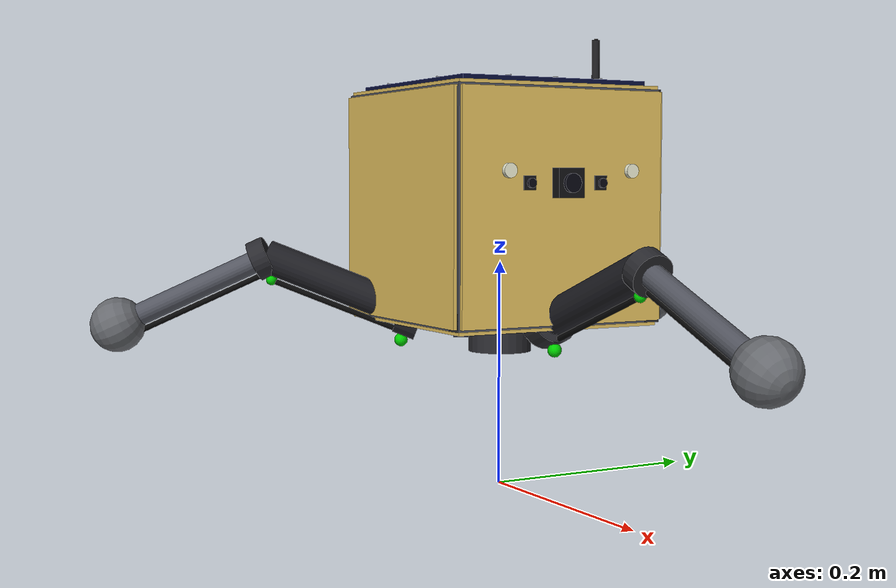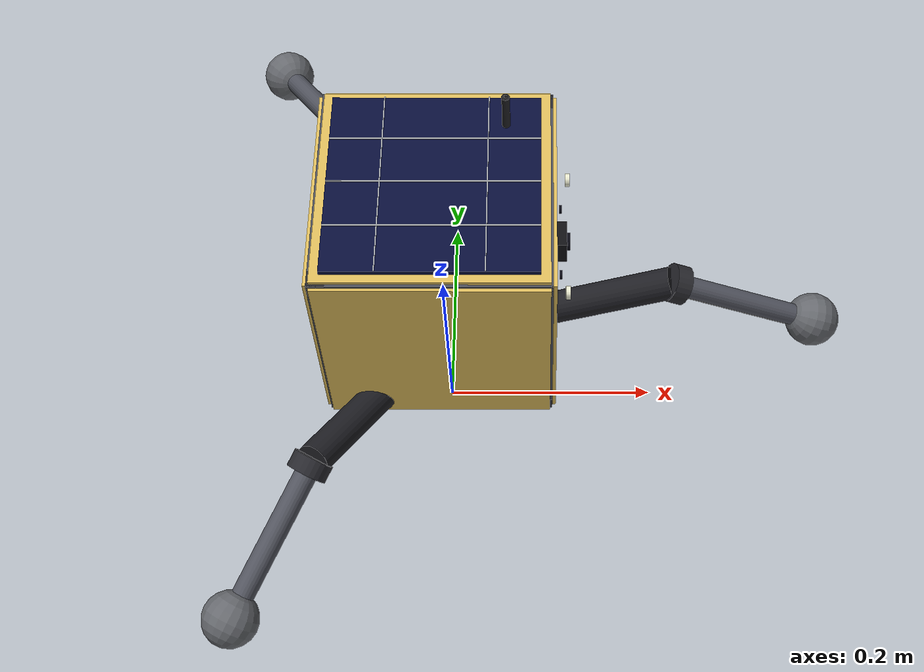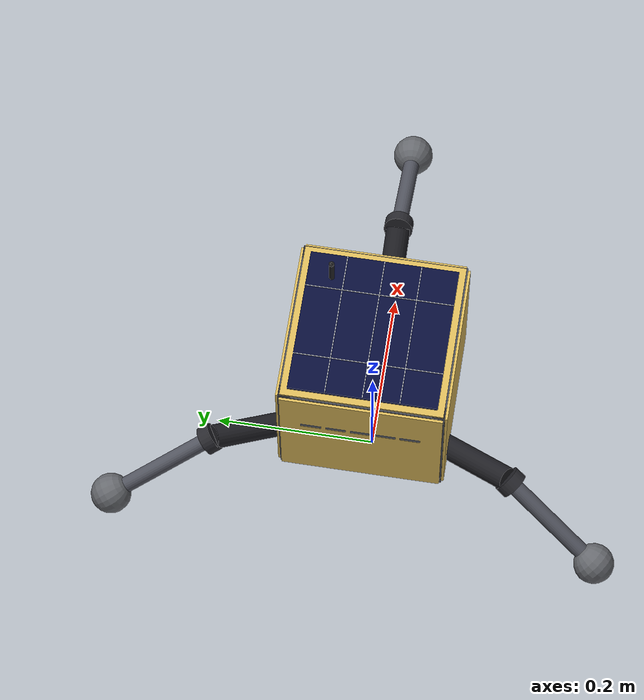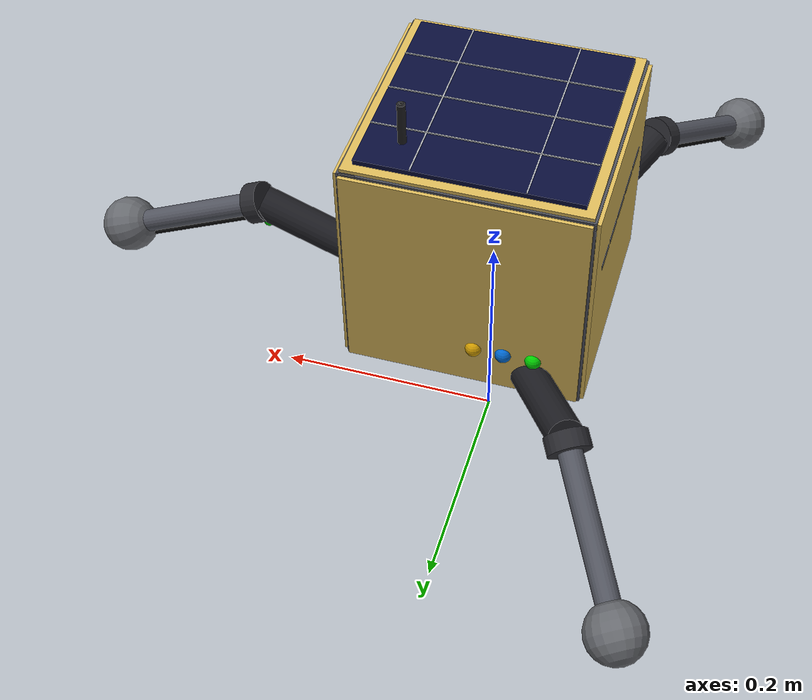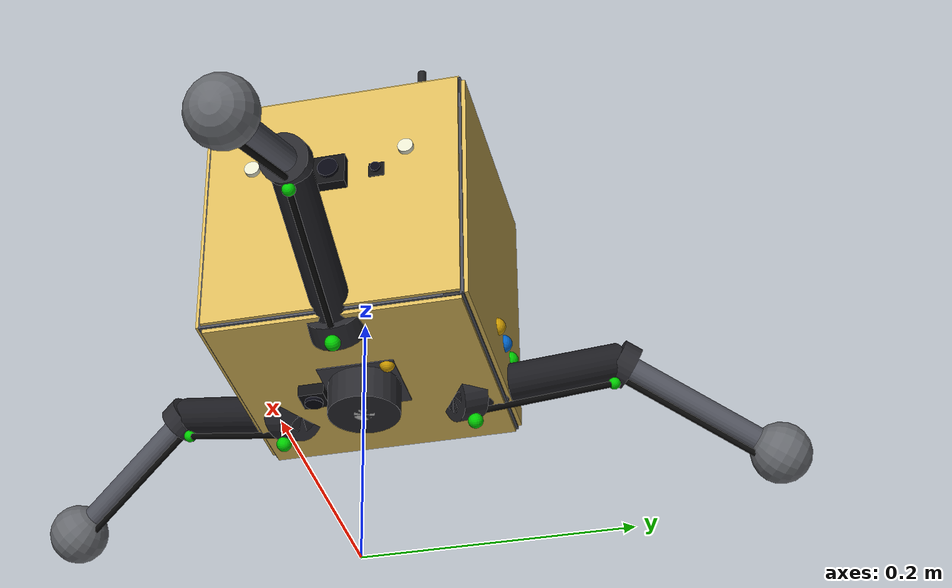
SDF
<?xml version="1.0" ?>
<sdf version="1.8">
  <model name="spacehopper">
    <allow_auto_disable>false</allow_auto_disable>

    <!-- ══════════ BASE CHASSIS ══════════ -->
    <link name="base_link">
      <pose>0 0 0.25 0 0 0</pose>
      <inertial>
        <pose>0.00243 0.0 -0.00703 0 0 0</pose>
        <mass>1.3839</mass>
        <inertia>
          <ixx>0.009844</ixx><ixy>-0.000090</ixy><ixz>-0.000123</ixz>
          <iyy>0.010118</iyy><iyz>-0.000008</iyz>
          <izz>0.007611</izz>
        </inertia>
      </inertial>

      <!-- Main hull - brushed aluminum structural panel -->
      <visual name="hull_visual">
        <geometry><box><size>0.2 0.2 0.2</size></box></geometry>
        <material>
          <ambient>0.3 0.31 0.35 1</ambient>
          <diffuse>0.3 0.31 0.35 1</diffuse>
          <specular>0.5 0.5 0.5 1</specular>
          <pbr>
            <metal>
              <metalness>0.75</metalness>
              <roughness>0.28</roughness>
            </metal>
          </pbr>
        </material>
      </visual>

      <visual name="seam_front">
        <pose>0.0995 0 0.02 0 0 0</pose>
        <geometry><box><size>0.001 0.196 0.003</size></box></geometry>
        <material>
          <ambient>0.04 0.04 0.045 1</ambient>
          <diffuse>0.04 0.04 0.045 1</diffuse>
          <specular>0.5 0.5 0.5 1</specular>
          <pbr>
            <metal>
              <metalness>0.3</metalness>
              <roughness>0.85</roughness>
            </metal>
          </pbr>
        </material>
      </visual>
      <visual name="seam_back">
        <pose>-0.0995 0 0.02 0 0 0</pose>
        <geometry><box><size>0.001 0.196 0.003</size></box></geometry>
        <material>
          <ambient>0.04 0.04 0.045 1</ambient>
          <diffuse>0.04 0.04 0.045 1</diffuse>
          <specular>0.5 0.5 0.5 1</specular>
          <pbr>
            <metal>
              <metalness>0.3</metalness>
              <roughness>0.85</roughness>
            </metal>
          </pbr>
        </material>
      </visual>
      <visual name="seam_left">
        <pose>0 0.0995 0.02 0 0 0</pose>
        <geometry><box><size>0.196 0.001 0.003</size></box></geometry>
        <material>
          <ambient>0.04 0.04 0.045 1</ambient>
          <diffuse>0.04 0.04 0.045 1</diffuse>
          <specular>0.5 0.5 0.5 1</specular>
          <pbr>
            <metal>
              <metalness>0.3</metalness>
              <roughness>0.85</roughness>
            </metal>
          </pbr>
        </material>
      </visual>
      <visual name="seam_right">
        <pose>0 -0.0995 0.02 0 0 0</pose>
        <geometry><box><size>0.196 0.001 0.003</size></box></geometry>
        <material>
          <ambient>0.04 0.04 0.045 1</ambient>
          <diffuse>0.04 0.04 0.045 1</diffuse>
          <specular>0.5 0.5 0.5 1</specular>
          <pbr>
            <metal>
              <metalness>0.3</metalness>
              <roughness>0.85</roughness>
            </metal>
          </pbr>
        </material>
      </visual>

      <visual name="hull_bolt_0">
        <pose>0.099 0.085 0.085 0 1.5708 0</pose>
        <geometry><cylinder><radius>0.003</radius><length>0.004</length></cylinder></geometry>
        <material>
          <ambient>0.16 0.16 0.18 1</ambient>
          <diffuse>0.16 0.16 0.18 1</diffuse>
          <specular>0.5 0.5 0.5 1</specular>
          <pbr>
            <metal>
              <metalness>0.85</metalness>
              <roughness>0.25</roughness>
            </metal>
          </pbr>
        </material>
      </visual>
      <visual name="hull_bolt_1">
        <pose>0.099 -0.085 0.085 0 1.5708 0</pose>
        <geometry><cylinder><radius>0.003</radius><length>0.004</length></cylinder></geometry>
        <material>
          <ambient>0.16 0.16 0.18 1</ambient>
          <diffuse>0.16 0.16 0.18 1</diffuse>
          <specular>0.5 0.5 0.5 1</specular>
          <pbr>
            <metal>
              <metalness>0.85</metalness>
              <roughness>0.25</roughness>
            </metal>
          </pbr>
        </material>
      </visual>
      <visual name="hull_bolt_2">
        <pose>0.099 0.085 -0.085 0 1.5708 0</pose>
        <geometry><cylinder><radius>0.003</radius><length>0.004</length></cylinder></geometry>
        <material>
          <ambient>0.16 0.16 0.18 1</ambient>
          <diffuse>0.16 0.16 0.18 1</diffuse>
          <specular>0.5 0.5 0.5 1</specular>
          <pbr>
            <metal>
              <metalness>0.85</metalness>
              <roughness>0.25</roughness>
            </metal>
          </pbr>
        </material>
      </visual>
      <visual name="hull_bolt_3">
        <pose>0.099 -0.085 -0.085 0 1.5708 0</pose>
        <geometry><cylinder><radius>0.003</radius><length>0.004</length></cylinder></geometry>
        <material>
          <ambient>0.16 0.16 0.18 1</ambient>
          <diffuse>0.16 0.16 0.18 1</diffuse>
          <specular>0.5 0.5 0.5 1</specular>
          <pbr>
            <metal>
              <metalness>0.85</metalness>
              <roughness>0.25</roughness>
            </metal>
          </pbr>
        </material>
      </visual>
      <visual name="hull_bolt_4">
        <pose>0.099 0 0.085 0 1.5708 0</pose>
        <geometry><cylinder><radius>0.003</radius><length>0.004</length></cylinder></geometry>
        <material>
          <ambient>0.16 0.16 0.18 1</ambient>
          <diffuse>0.16 0.16 0.18 1</diffuse>
          <specular>0.5 0.5 0.5 1</specular>
          <pbr>
            <metal>
              <metalness>0.85</metalness>
              <roughness>0.25</roughness>
            </metal>
          </pbr>
        </material>
      </visual>
      <visual name="hull_bolt_5">
        <pose>0.099 0 -0.085 0 1.5708 0</pose>
        <geometry><cylinder><radius>0.003</radius><length>0.004</length></cylinder></geometry>
        <material>
          <ambient>0.16 0.16 0.18 1</ambient>
          <diffuse>0.16 0.16 0.18 1</diffuse>
          <specular>0.5 0.5 0.5 1</specular>
          <pbr>
            <metal>
              <metalness>0.85</metalness>
              <roughness>0.25</roughness>
            </metal>
          </pbr>
        </material>
      </visual>

      <!-- ── MLI thermal blankets ── -->

      <visual name="mli_top">
        <pose>0 0 0.1015 0 0 0</pose>
        <geometry><box><size>0.196 0.196 0.003</size></box></geometry>
        <material>
          <ambient>0.85 0.72 0.35 1</ambient>
          <diffuse>0.85 0.72 0.35 1</diffuse>
          <specular>0.5 0.5 0.5 1</specular>
          <pbr>
            <metal>
              <metalness>0.9</metalness>
              <roughness>0.15</roughness>
            </metal>
          </pbr>
        </material>
      </visual>
      <visual name="mli_bottom">
        <pose>0 0 -0.1015 0 0 0</pose>
        <geometry><box><size>0.196 0.196 0.003</size></box></geometry>
        <material>
          <ambient>0.85 0.72 0.35 1</ambient>
          <diffuse>0.85 0.72 0.35 1</diffuse>
          <specular>0.5 0.5 0.5 1</specular>
          <pbr>
            <metal>
              <metalness>0.9</metalness>
              <roughness>0.15</roughness>
            </metal>
          </pbr>
        </material>
      </visual>
      <visual name="mli_front">
        <pose>0.1015 0 0 0 0 0</pose>
        <geometry><box><size>0.003 0.196 0.196</size></box></geometry>
        <material>
          <ambient>0.85 0.72 0.35 1</ambient>
          <diffuse>0.85 0.72 0.35 1</diffuse>
          <specular>0.5 0.5 0.5 1</specular>
          <pbr>
            <metal>
              <metalness>0.9</metalness>
              <roughness>0.15</roughness>
            </metal>
          </pbr>
        </material>
      </visual>
      <visual name="mli_back">
        <pose>-0.1015 0 0 0 0 0</pose>
        <geometry><box><size>0.003 0.196 0.196</size></box></geometry>
        <material>
          <ambient>0.85 0.72 0.35 1</ambient>
          <diffuse>0.85 0.72 0.35 1</diffuse>
          <specular>0.5 0.5 0.5 1</specular>
          <pbr>
            <metal>
              <metalness>0.9</metalness>
              <roughness>0.15</roughness>
            </metal>
          </pbr>
        </material>
      </visual>
      <visual name="mli_left">
        <pose>0 0.1015 0 0 0 0</pose>
        <geometry><box><size>0.196 0.003 0.196</size></box></geometry>
        <material>
          <ambient>0.85 0.72 0.35 1</ambient>
          <diffuse>0.85 0.72 0.35 1</diffuse>
          <specular>0.5 0.5 0.5 1</specular>
          <pbr>
            <metal>
              <metalness>0.9</metalness>
              <roughness>0.15</roughness>
            </metal>
          </pbr>
        </material>
      </visual>
      <visual name="mli_right">
        <pose>0 -0.1015 0 0 0 0</pose>
        <geometry><box><size>0.196 0.003 0.196</size></box></geometry>
        <material>
          <ambient>0.85 0.72 0.35 1</ambient>
          <diffuse>0.85 0.72 0.35 1</diffuse>
          <specular>0.5 0.5 0.5 1</specular>
          <pbr>
            <metal>
              <metalness>0.9</metalness>
              <roughness>0.15</roughness>
            </metal>
          </pbr>
        </material>
      </visual>

      <!-- ── Structural corner brackets ── -->

      <visual name="bracket_0">
        <pose>-0.0925 -0.0925 -0.0925 0 0 0</pose>
        <geometry><box><size>0.015 0.015 0.015</size></box></geometry>
        <material>
          <ambient>0.16 0.16 0.18 1</ambient>
          <diffuse>0.16 0.16 0.18 1</diffuse>
          <specular>0.5 0.5 0.5 1</specular>
          <pbr>
            <metal>
              <metalness>0.8</metalness>
              <roughness>0.3</roughness>
            </metal>
          </pbr>
        </material>
      </visual>
      <visual name="bracket_1">
        <pose>-0.0925 -0.0925 0.0925 0 0 0</pose>
        <geometry><box><size>0.015 0.015 0.015</size></box></geometry>
        <material>
          <ambient>0.16 0.16 0.18 1</ambient>
          <diffuse>0.16 0.16 0.18 1</diffuse>
          <specular>0.5 0.5 0.5 1</specular>
          <pbr>
            <metal>
              <metalness>0.8</metalness>
              <roughness>0.3</roughness>
            </metal>
          </pbr>
        </material>
      </visual>
      <visual name="bracket_2">
        <pose>-0.0925 0.0925 -0.0925 0 0 0</pose>
        <geometry><box><size>0.015 0.015 0.015</size></box></geometry>
        <material>
          <ambient>0.16 0.16 0.18 1</ambient>
          <diffuse>0.16 0.16 0.18 1</diffuse>
          <specular>0.5 0.5 0.5 1</specular>
          <pbr>
            <metal>
              <metalness>0.8</metalness>
              <roughness>0.3</roughness>
            </metal>
          </pbr>
        </material>
      </visual>
      <visual name="bracket_3">
        <pose>-0.0925 0.0925 0.0925 0 0 0</pose>
        <geometry><box><size>0.015 0.015 0.015</size></box></geometry>
        <material>
          <ambient>0.16 0.16 0.18 1</ambient>
          <diffuse>0.16 0.16 0.18 1</diffuse>
          <specular>0.5 0.5 0.5 1</specular>
          <pbr>
            <metal>
              <metalness>0.8</metalness>
              <roughness>0.3</roughness>
            </metal>
          </pbr>
        </material>
      </visual>
      <visual name="bracket_4">
        <pose>0.0925 -0.0925 -0.0925 0 0 0</pose>
        <geometry><box><size>0.015 0.015 0.015</size></box></geometry>
        <material>
          <ambient>0.16 0.16 0.18 1</ambient>
          <diffuse>0.16 0.16 0.18 1</diffuse>
          <specular>0.5 0.5 0.5 1</specular>
          <pbr>
            <metal>
              <metalness>0.8</metalness>
              <roughness>0.3</roughness>
            </metal>
          </pbr>
        </material>
      </visual>
      <visual name="bracket_5">
        <pose>0.0925 -0.0925 0.0925 0 0 0</pose>
        <geometry><box><size>0.015 0.015 0.015</size></box></geometry>
        <material>
          <ambient>0.16 0.16 0.18 1</ambient>
          <diffuse>0.16 0.16 0.18 1</diffuse>
          <specular>0.5 0.5 0.5 1</specular>
          <pbr>
            <metal>
              <metalness>0.8</metalness>
              <roughness>0.3</roughness>
            </metal>
          </pbr>
        </material>
      </visual>
      <visual name="bracket_6">
        <pose>0.0925 0.0925 -0.0925 0 0 0</pose>
        <geometry><box><size>0.015 0.015 0.015</size></box></geometry>
        <material>
          <ambient>0.16 0.16 0.18 1</ambient>
          <diffuse>0.16 0.16 0.18 1</diffuse>
          <specular>0.5 0.5 0.5 1</specular>
          <pbr>
            <metal>
              <metalness>0.8</metalness>
              <roughness>0.3</roughness>
            </metal>
          </pbr>
        </material>
      </visual>
      <visual name="bracket_7">
        <pose>0.0925 0.0925 0.0925 0 0 0</pose>
        <geometry><box><size>0.015 0.015 0.015</size></box></geometry>
        <material>
          <ambient>0.16 0.16 0.18 1</ambient>
          <diffuse>0.16 0.16 0.18 1</diffuse>
          <specular>0.5 0.5 0.5 1</specular>
          <pbr>
            <metal>
              <metalness>0.8</metalness>
              <roughness>0.3</roughness>
            </metal>
          </pbr>
        </material>
      </visual>

      <!-- ── Antenna ── -->

      <visual name="antenna_mast">
        <pose>0.06 0.06 0.122 0 0 0</pose>
        <geometry><cylinder><radius>0.0035</radius><length>0.044</length></cylinder></geometry>
        <material>
          <ambient>0.12 0.12 0.13 1</ambient>
          <diffuse>0.12 0.12 0.13 1</diffuse>
          <specular>0.5 0.5 0.5 1</specular>
          <pbr>
            <metal>
              <metalness>0.7</metalness>
              <roughness>0.35</roughness>
            </metal>
          </pbr>
        </material>
      </visual>
      <visual name="antenna_base_collar">
        <pose>0.06 0.06 0.101 0 0 0</pose>
        <geometry><cylinder><radius>0.008</radius><length>0.006</length></cylinder></geometry>
        <material>
          <ambient>0.16 0.16 0.18 1</ambient>
          <diffuse>0.16 0.16 0.18 1</diffuse>
          <specular>0.5 0.5 0.5 1</specular>
          <pbr>
            <metal>
              <metalness>0.8</metalness>
              <roughness>0.3</roughness>
            </metal>
          </pbr>
        </material>
      </visual>
      <visual name="antenna_tip">
        <pose>0.06 0.06 0.1445 0 0 0</pose>
        <geometry><cylinder><radius>0.0015</radius><length>0.001</length></cylinder></geometry>
        <material>
          <ambient>0.05 0.05 0.05 1</ambient>
          <diffuse>0.05 0.05 0.05 1</diffuse>
          <specular>0.5 0.5 0.5 1</specular>
          <pbr>
            <metal>
              <metalness>0.6</metalness>
              <roughness>0.5</roughness>
            </metal>
          </pbr>
        </material>
      </visual>
      <!-- S-Band patch antenna (flat plate, per Research_Paper.md §4.2) -->
      <visual name="antenna_patch">
        <pose>-0.04 -0.06 0.101 0 0 0.4</pose>
        <geometry><box><size>0.03 0.03 0.003</size></box></geometry>
        <material>
          <ambient>0.5 0.51 0.55 1</ambient>
          <diffuse>0.5 0.51 0.55 1</diffuse>
          <specular>0.5 0.5 0.5 1</specular>
          <pbr>
            <metal>
              <metalness>0.6</metalness>
              <roughness>0.35</roughness>
            </metal>
          </pbr>
        </material>
      </visual>
      <visual name="antenna_patch_frame">
        <pose>-0.04 -0.06 0.0995 0 0 0.4</pose>
        <geometry><box><size>0.034 0.034 0.001</size></box></geometry>
        <material>
          <ambient>0.16 0.16 0.18 1</ambient>
          <diffuse>0.16 0.16 0.18 1</diffuse>
          <specular>0.5 0.5 0.5 1</specular>
          <pbr>
            <metal>
              <metalness>0.75</metalness>
              <roughness>0.3</roughness>
            </metal>
          </pbr>
        </material>
      </visual>
      <!-- Comms status LED at the antenna base -->
      <visual name="comms_led">
        <pose>0.06 0.048 0.101 0 0 0</pose>
        <geometry><sphere><radius>0.005</radius></sphere></geometry>
        <material>
          <ambient>0.0 0.4 0.8 1</ambient>
          <diffuse>0.0 0.4 0.8 1</diffuse>
          <specular>0.3 0.3 0.3 1</specular>
          <emissive>0.0 0.5 1.0 1</emissive>
        </material>
      </visual>

      <light type="point" name="comms_led_light">
        <pose>0.06 0.048 0.101 0 0 0</pose>
        <diffuse>0.0 0.5 1.0 1</diffuse>
        <specular>0.0 0.5 1.0 1</specular>
        <intensity>3.0</intensity>
        <attenuation>
          <range>0.05</range>
          <constant>0.15</constant>
          <linear>2.5</linear>
          <quadratic>6</quadratic>
        </attenuation>
        <cast_shadows>false</cast_shadows>
        <visualize>false</visualize>
      </light>

      <!-- ── Cameras ── -->

      <!-- Nav-cam floodlights (real spotlights, forward-facing) -->

      <light type="spot" name="headlight_left">
        <pose>0.11 0.06 0.03 0 0 0</pose>
        <diffuse>1.0 0.98 0.9 1</diffuse>
        <specular>1.0 0.98 0.9 1</specular>
        <intensity>6.0</intensity>
        <direction>1 0 0</direction>
        <attenuation>
          <range>1.2</range>
          <constant>0.1</constant>
          <linear>1.0</linear>
          <quadratic>1.5</quadratic>
        </attenuation>
        <spot>
          <inner_angle>0.4</inner_angle>
          <outer_angle>0.7</outer_angle>
          <falloff>1.0</falloff>
        </spot>
        <cast_shadows>false</cast_shadows>
        <visualize>false</visualize>
      </light>

      <light type="spot" name="headlight_right">
        <pose>0.11 -0.06 0.03 0 0 0</pose>
        <diffuse>1.0 0.98 0.9 1</diffuse>
        <specular>1.0 0.98 0.9 1</specular>
        <intensity>6.0</intensity>
        <direction>1 0 0</direction>
        <attenuation>
          <range>1.2</range>
          <constant>0.1</constant>
          <linear>1.0</linear>
          <quadratic>1.5</quadratic>
        </attenuation>
        <spot>
          <inner_angle>0.4</inner_angle>
          <outer_angle>0.7</outer_angle>
          <falloff>1.0</falloff>
        </spot>
        <cast_shadows>false</cast_shadows>
        <visualize>false</visualize>
      </light>
      <visual name="headlight_left_lens">
        <pose>0.113 0.06 0.03 0 1.5708 0</pose>
        <geometry><cylinder><radius>0.006</radius><length>0.004</length></cylinder></geometry>
        <material>
          <ambient>0.9 0.9 0.8 1</ambient>
          <diffuse>0.9 0.9 0.8 1</diffuse>
          <specular>0.3 0.3 0.3 1</specular>
          <emissive>1.0 1.0 0.9 1</emissive>
        </material>
      </visual>
      <visual name="headlight_right_lens">
        <pose>0.113 -0.06 0.03 0 1.5708 0</pose>
        <geometry><cylinder><radius>0.006</radius><length>0.004</length></cylinder></geometry>
        <material>
          <ambient>0.9 0.9 0.8 1</ambient>
          <diffuse>0.9 0.9 0.8 1</diffuse>
          <specular>0.3 0.3 0.3 1</specular>
          <emissive>1.0 1.0 0.9 1</emissive>
        </material>
      </visual>
      <!-- Navigation camera -->
      <visual name="camera_body">
        <pose>0.105 0 0.02 0 0 0</pose>
        <geometry><box><size>0.015 0.025 0.025</size></box></geometry>
        <material>
          <ambient>0.06 0.06 0.07 1</ambient>
          <diffuse>0.06 0.06 0.07 1</diffuse>
          <specular>0.5 0.5 0.5 1</specular>
          <pbr>
            <metal>
              <metalness>0.55</metalness>
              <roughness>0.45</roughness>
            </metal>
          </pbr>
        </material>
      </visual>
      <visual name="camera_lens">
        <pose>0.114 0 0.02 0 1.5708 0</pose>
        <geometry><cylinder><radius>0.008</radius><length>0.003</length></cylinder></geometry>
        <material>
          <ambient>0.02 0.02 0.06 1</ambient>
          <diffuse>0.02 0.02 0.06 1</diffuse>
          <specular>0.5 0.5 0.5 1</specular>
          <pbr>
            <metal>
              <metalness>0.9</metalness>
              <roughness>0.1</roughness>
            </metal>
          </pbr>
        </material>
      </visual>
      <!-- Science camera (bottom-mounted, downward-facing) -->
      <visual name="sci_camera_body">
        <pose>0 -0.04 -0.105 0 0 0</pose>
        <geometry><box><size>0.02 0.02 0.015</size></box></geometry>
        <material>
          <ambient>0.06 0.06 0.07 1</ambient>
          <diffuse>0.06 0.06 0.07 1</diffuse>
          <specular>0.5 0.5 0.5 1</specular>
          <pbr>
            <metal>
              <metalness>0.55</metalness>
              <roughness>0.45</roughness>
            </metal>
          </pbr>
        </material>
      </visual>
      <visual name="sci_camera_lens">
        <pose>0 -0.04 -0.114 0 0 0</pose>
        <geometry><cylinder><radius>0.007</radius><length>0.003</length></cylinder></geometry>
        <material>
          <ambient>0.02 0.02 0.06 1</ambient>
          <diffuse>0.02 0.02 0.06 1</diffuse>
          <specular>0.5 0.5 0.5 1</specular>
          <pbr>
            <metal>
              <metalness>0.9</metalness>
              <roughness>0.1</roughness>
            </metal>
          </pbr>
        </material>
      </visual>
      <visual name="hazcam_left_body">
        <pose>0.100 0.035 0.02 0 0 0</pose>
        <geometry><box><size>0.008 0.012 0.012</size></box></geometry>
        <material>
          <ambient>0.06 0.06 0.07 1</ambient>
          <diffuse>0.06 0.06 0.07 1</diffuse>
          <specular>0.5 0.5 0.5 1</specular>
          <pbr>
            <metal>
              <metalness>0.55</metalness>
              <roughness>0.45</roughness>
            </metal>
          </pbr>
        </material>
      </visual>
      <visual name="hazcam_left_lens">
        <pose>0.107 0.035 0.02 0 1.5708 0</pose>
        <geometry><cylinder><radius>0.004</radius><length>0.002</length></cylinder></geometry>
        <material>
          <ambient>0.02 0.02 0.06 1</ambient>
          <diffuse>0.02 0.02 0.06 1</diffuse>
          <specular>0.5 0.5 0.5 1</specular>
          <pbr>
            <metal>
              <metalness>0.9</metalness>
              <roughness>0.1</roughness>
            </metal>
          </pbr>
        </material>
      </visual>
      <visual name="hazcam_right_body">
        <pose>0.100 -0.035 0.02 0 0 0</pose>
        <geometry><box><size>0.008 0.012 0.012</size></box></geometry>
        <material>
          <ambient>0.06 0.06 0.07 1</ambient>
          <diffuse>0.06 0.06 0.07 1</diffuse>
          <specular>0.5 0.5 0.5 1</specular>
          <pbr>
            <metal>
              <metalness>0.55</metalness>
              <roughness>0.45</roughness>
            </metal>
          </pbr>
        </material>
      </visual>
      <visual name="hazcam_right_lens">
        <pose>0.107 -0.035 0.02 0 1.5708 0</pose>
        <geometry><cylinder><radius>0.004</radius><length>0.002</length></cylinder></geometry>
        <material>
          <ambient>0.02 0.02 0.06 1</ambient>
          <diffuse>0.02 0.02 0.06 1</diffuse>
          <specular>0.5 0.5 0.5 1</specular>
          <pbr>
            <metal>
              <metalness>0.9</metalness>
              <roughness>0.1</roughness>
            </metal>
          </pbr>
        </material>
      </visual>

      <!-- ── Thermal louvers ── -->

      <visual name="louver_0">
        <pose>-0.102 -0.06 0.03 0 0 0</pose>
        <geometry><box><size>0.003 0.025 0.005</size></box></geometry>
        <material>
          <ambient>0.4 0.41 0.44 1</ambient>
          <diffuse>0.4 0.41 0.44 1</diffuse>
          <specular>0.5 0.5 0.5 1</specular>
          <pbr>
            <metal>
              <metalness>0.7</metalness>
              <roughness>0.3</roughness>
            </metal>
          </pbr>
        </material>
      </visual>
      <visual name="louver_1">
        <pose>-0.102 -0.03 0.03 0 0 0</pose>
        <geometry><box><size>0.003 0.025 0.005</size></box></geometry>
        <material>
          <ambient>0.4 0.41 0.44 1</ambient>
          <diffuse>0.4 0.41 0.44 1</diffuse>
          <specular>0.5 0.5 0.5 1</specular>
          <pbr>
            <metal>
              <metalness>0.7</metalness>
              <roughness>0.3</roughness>
            </metal>
          </pbr>
        </material>
      </visual>
      <visual name="louver_2">
        <pose>-0.102 0.0 0.03 0 0 0</pose>
        <geometry><box><size>0.003 0.025 0.005</size></box></geometry>
        <material>
          <ambient>0.4 0.41 0.44 1</ambient>
          <diffuse>0.4 0.41 0.44 1</diffuse>
          <specular>0.5 0.5 0.5 1</specular>
          <pbr>
            <metal>
              <metalness>0.7</metalness>
              <roughness>0.3</roughness>
            </metal>
          </pbr>
        </material>
      </visual>
      <visual name="louver_3">
        <pose>-0.102 0.03 0.03 0 0 0</pose>
        <geometry><box><size>0.003 0.025 0.005</size></box></geometry>
        <material>
          <ambient>0.4 0.41 0.44 1</ambient>
          <diffuse>0.4 0.41 0.44 1</diffuse>
          <specular>0.5 0.5 0.5 1</specular>
          <pbr>
            <metal>
              <metalness>0.7</metalness>
              <roughness>0.3</roughness>
            </metal>
          </pbr>
        </material>
      </visual>
      <visual name="louver_4">
        <pose>-0.102 0.06 0.03 0 0 0</pose>
        <geometry><box><size>0.003 0.025 0.005</size></box></geometry>
        <material>
          <ambient>0.4 0.41 0.44 1</ambient>
          <diffuse>0.4 0.41 0.44 1</diffuse>
          <specular>0.5 0.5 0.5 1</specular>
          <pbr>
            <metal>
              <metalness>0.7</metalness>
              <roughness>0.3</roughness>
            </metal>
          </pbr>
        </material>
      </visual>

      <!-- ── Status LEDs ── -->

      <visual name="led_0">
        <pose>-0.06 0.102 -0.06 0 0 0</pose>
        <geometry><sphere><radius>0.007</radius></sphere></geometry>
        <material>
          <ambient>0.0 0.8 0.0 1</ambient>
          <diffuse>0.0 0.8 0.0 1</diffuse>
          <specular>0.3 0.3 0.3 1</specular>
          <emissive>0.0 1.0 0.0 1</emissive>
        </material>
      </visual>

      <light type="point" name="led_0_light">
        <pose>-0.06 0.102 -0.06 0 0 0</pose>
        <diffuse>0.0 1.0 0.0 1</diffuse>
        <specular>0.0 1.0 0.0 1</specular>
        <intensity>3.0</intensity>
        <attenuation>
          <range>0.12</range>
          <constant>0.15</constant>
          <linear>2.5</linear>
          <quadratic>6</quadratic>
        </attenuation>
        <cast_shadows>false</cast_shadows>
        <visualize>false</visualize>
      </light>
      <visual name="led_1">
        <pose>-0.034999999999999996 0.102 -0.06 0 0 0</pose>
        <geometry><sphere><radius>0.007</radius></sphere></geometry>
        <material>
          <ambient>0.0 0.4 0.8 1</ambient>
          <diffuse>0.0 0.4 0.8 1</diffuse>
          <specular>0.3 0.3 0.3 1</specular>
          <emissive>0.0 0.5 1.0 1</emissive>
        </material>
      </visual>

      <light type="point" name="led_1_light">
        <pose>-0.034999999999999996 0.102 -0.06 0 0 0</pose>
        <diffuse>0.0 0.5 1.0 1</diffuse>
        <specular>0.0 0.5 1.0 1</specular>
        <intensity>3.0</intensity>
        <attenuation>
          <range>0.12</range>
          <constant>0.15</constant>
          <linear>2.5</linear>
          <quadratic>6</quadratic>
        </attenuation>
        <cast_shadows>false</cast_shadows>
        <visualize>false</visualize>
      </light>
      <visual name="led_2">
        <pose>-0.009999999999999995 0.102 -0.06 0 0 0</pose>
        <geometry><sphere><radius>0.007</radius></sphere></geometry>
        <material>
          <ambient>0.8 0.6 0.0 1</ambient>
          <diffuse>0.8 0.6 0.0 1</diffuse>
          <specular>0.3 0.3 0.3 1</specular>
          <emissive>1.0 0.8 0.0 1</emissive>
        </material>
      </visual>

      <light type="point" name="led_2_light">
        <pose>-0.009999999999999995 0.102 -0.06 0 0 0</pose>
        <diffuse>1.0 0.8 0.0 1</diffuse>
        <specular>1.0 0.8 0.0 1</specular>
        <intensity>3.0</intensity>
        <attenuation>
          <range>0.12</range>
          <constant>0.15</constant>
          <linear>2.5</linear>
          <quadratic>6</quadratic>
        </attenuation>
        <cast_shadows>false</cast_shadows>
        <visualize>false</visualize>
      </light>

      <!-- Internal visuals removed to prevent clipping -->

      <!-- ── Reaction wheel housings ── -->

      <!-- RW protective housings -->
      <visual name="rw_housing_x">
        <pose>0 0 0 0 1.5707963267948966 0</pose>
        <geometry><cylinder><radius>0.065</radius><length>0.005</length></cylinder></geometry>
        <material>
          <ambient>0.2 0.2 0.22 1</ambient>
          <diffuse>0.2 0.2 0.22 1</diffuse>
          <specular>0.5 0.5 0.5 1</specular>
          <pbr>
            <metal>
              <metalness>0.75</metalness>
              <roughness>0.3</roughness>
            </metal>
          </pbr>
        </material>
      </visual>
      <visual name="rw_housing_y">
        <pose>0 0 0 1.5707963267948966 0 0</pose>
        <geometry><cylinder><radius>0.065</radius><length>0.005</length></cylinder></geometry>
        <material>
          <ambient>0.2 0.2 0.22 1</ambient>
          <diffuse>0.2 0.2 0.22 1</diffuse>
          <specular>0.5 0.5 0.5 1</specular>
          <pbr>
            <metal>
              <metalness>0.75</metalness>
              <roughness>0.3</roughness>
            </metal>
          </pbr>
        </material>
      </visual>
      <visual name="rw_housing_z">
        <pose>0 0 0 0 0 0</pose>
        <geometry><cylinder><radius>0.065</radius><length>0.005</length></cylinder></geometry>
        <material>
          <ambient>0.2 0.2 0.22 1</ambient>
          <diffuse>0.2 0.2 0.22 1</diffuse>
          <specular>0.5 0.5 0.5 1</specular>
          <pbr>
            <metal>
              <metalness>0.75</metalness>
              <roughness>0.3</roughness>
            </metal>
          </pbr>
        </material>
      </visual>
      <visual name="rw_led_x">
        <pose>0.066 0 0 0 1.5708 0</pose>
        <geometry><sphere><radius>0.006</radius></sphere></geometry>
        <material>
          <ambient>0.0 0.5 1.0 1</ambient>
          <diffuse>0.0 0.5 1.0 1</diffuse>
          <specular>0.3 0.3 0.3 1</specular>
          <emissive>0.0 0.5 1.0 1</emissive>
        </material>
      </visual>

      <light type="point" name="rw_led_x_light">
        <pose>0.066 0 0 0 1.5708 0</pose>
        <diffuse>0.0 0.5 1.0 1</diffuse>
        <specular>0.0 0.5 1.0 1</specular>
        <intensity>3.0</intensity>
        <attenuation>
          <range>0.05</range>
          <constant>0.15</constant>
          <linear>2.5</linear>
          <quadratic>6</quadratic>
        </attenuation>
        <cast_shadows>false</cast_shadows>
        <visualize>false</visualize>
      </light>
      <visual name="rw_led_y">
        <pose>0 0.066 0 1.5708 0 0</pose>
        <geometry><sphere><radius>0.006</radius></sphere></geometry>
        <material>
          <ambient>0.0 0.5 1.0 1</ambient>
          <diffuse>0.0 0.5 1.0 1</diffuse>
          <specular>0.3 0.3 0.3 1</specular>
          <emissive>0.0 0.5 1.0 1</emissive>
        </material>
      </visual>

      <light type="point" name="rw_led_y_light">
        <pose>0 0.066 0 1.5708 0 0</pose>
        <diffuse>0.0 0.5 1.0 1</diffuse>
        <specular>0.0 0.5 1.0 1</specular>
        <intensity>3.0</intensity>
        <attenuation>
          <range>0.05</range>
          <constant>0.15</constant>
          <linear>2.5</linear>
          <quadratic>6</quadratic>
        </attenuation>
        <cast_shadows>false</cast_shadows>
        <visualize>false</visualize>
      </light>
      <visual name="rw_led_z">
        <pose>0 0 0.066 0 0 0</pose>
        <geometry><sphere><radius>0.006</radius></sphere></geometry>
        <material>
          <ambient>0.0 0.5 1.0 1</ambient>
          <diffuse>0.0 0.5 1.0 1</diffuse>
          <specular>0.3 0.3 0.3 1</specular>
          <emissive>0.0 0.5 1.0 1</emissive>
        </material>
      </visual>

      <light type="point" name="rw_led_z_light">
        <pose>0 0 0.066 0 0 0</pose>
        <diffuse>0.0 0.5 1.0 1</diffuse>
        <specular>0.0 0.5 1.0 1</specular>
        <intensity>3.0</intensity>
        <attenuation>
          <range>0.05</range>
          <constant>0.15</constant>
          <linear>2.5</linear>
          <quadratic>6</quadratic>
        </attenuation>
        <cast_shadows>false</cast_shadows>
        <visualize>false</visualize>
      </light>

      <!-- ── Drill mounting turret ── -->

      <!-- ── Drill mounting turret (fixed housing, shaft retracts up into it) ── -->
      <visual name="drill_turret">
        <pose>0 0 -0.1125 0 0 0</pose>
        <geometry><cylinder><radius>0.028</radius><length>0.035</length></cylinder></geometry>
        <material>
          <ambient>0.16 0.16 0.18 1</ambient>
          <diffuse>0.16 0.16 0.18 1</diffuse>
          <specular>0.5 0.5 0.5 1</specular>
          <pbr>
            <metal>
              <metalness>0.75</metalness>
              <roughness>0.35</roughness>
            </metal>
          </pbr>
        </material>
      </visual>
      <visual name="drill_turret_plate">
        <pose>0 0 -0.10200000000000001 0 0 0</pose>
        <geometry><box><size>0.06 0.06 0.004</size></box></geometry>
        <material>
          <ambient>0.25 0.25 0.28 1</ambient>
          <diffuse>0.25 0.25 0.28 1</diffuse>
          <specular>0.5 0.5 0.5 1</specular>
          <pbr>
            <metal>
              <metalness>0.6</metalness>
              <roughness>0.4</roughness>
            </metal>
          </pbr>
        </material>
      </visual>
      <!-- Science/sampler status LED -->
      <visual name="drill_led">
        <pose>0.024 0.024 -0.10300000000000001 0 0 0</pose>
        <geometry><sphere><radius>0.006</radius></sphere></geometry>
        <material>
          <ambient>0.8 0.6 0.0 1</ambient>
          <diffuse>0.8 0.6 0.0 1</diffuse>
          <specular>0.3 0.3 0.3 1</specular>
          <emissive>1.0 0.8 0.0 1</emissive>
        </material>
      </visual>

      <light type="point" name="drill_led_light">
        <pose>0.024 0.024 -0.10300000000000001 0 0 0</pose>
        <diffuse>1.0 0.8 0.0 1</diffuse>
        <specular>1.0 0.8 0.0 1</specular>
        <intensity>3.0</intensity>
        <attenuation>
          <range>0.05</range>
          <constant>0.15</constant>
          <linear>2.5</linear>
          <quadratic>6</quadratic>
        </attenuation>
        <cast_shadows>false</cast_shadows>
        <visualize>false</visualize>
      </light>

      <!-- ── Chassis collision ── -->
      <collision name="collision">
        <geometry><box><size>0.2 0.2 0.2</size></box></geometry>
      </collision>

      <!-- ── IMU sensor ── -->
      <sensor name="imu_sensor" type="imu">
        <always_on>1</always_on>
        <update_rate>100</update_rate>
        <visualize>true</visualize>
      </sensor>

      <!-- LIDAR removed to prevent performance stuttering -->
    </link>

    <plugin filename="gz-sim-imu-system" name="gz::sim::systems::Imu"/>

    <plugin filename="gz-sim-odometry-publisher-system" name="gz::sim::systems::OdometryPublisher">
      <odom_frame>spacehopper/odom</odom_frame>
      <robot_base_frame>spacehopper/base</robot_base_frame>
      <odom_publish_frequency>20</odom_publish_frequency>
      <dimensions>3</dimensions>
    </plugin>

    <!-- ══════════ SOLAR PANEL ARRAY (fixed to chassis top) ══════════ -->
    <link name="solar_panel">
      <pose>0 0 0.355 0 0 0</pose>
      <inertial>
        <mass>0.0152</mass>
        <inertia>
          <ixx>0.000041</ixx><ixy>0.000000</ixy><ixz>0.000000</ixz>
          <iyy>0.000041</iyy><iyz>0.000000</iyz>
          <izz>0.000082</izz>
        </inertia>
      </inertial>
      <visual name="panel_surface">
        <geometry><box><size>0.18 0.18 0.005</size></box></geometry>
        <material>
          <ambient>0.03 0.05 0.22 1</ambient>
          <diffuse>0.03 0.05 0.22 1</diffuse>
          <specular>0.5 0.5 0.5 1</specular>
          <pbr>
            <metal>
              <metalness>0.7</metalness>
              <roughness>0.15</roughness>
            </metal>
          </pbr>
        </material>
      </visual>
      <!-- Solar cell grid lines -->
      <visual name="cell_grid_h1">
        <pose>0 0 0.003 0 0 0</pose>
        <geometry><box><size>0.18 0.001 0.001</size></box></geometry>
        <material>
          <ambient>0.75 0.76 0.78 1</ambient>
          <diffuse>0.75 0.76 0.78 1</diffuse>
          <specular>0.5 0.5 0.5 1</specular>
          <pbr>
            <metal>
              <metalness>0.9</metalness>
              <roughness>0.2</roughness>
            </metal>
          </pbr>
        </material>
      </visual>
      <visual name="cell_grid_h2">
        <pose>0 0.045 0.003 0 0 0</pose>
        <geometry><box><size>0.18 0.001 0.001</size></box></geometry>
        <material>
          <ambient>0.75 0.76 0.78 1</ambient>
          <diffuse>0.75 0.76 0.78 1</diffuse>
          <specular>0.5 0.5 0.5 1</specular>
          <pbr>
            <metal>
              <metalness>0.9</metalness>
              <roughness>0.2</roughness>
            </metal>
          </pbr>
        </material>
      </visual>
      <visual name="cell_grid_h3">
        <pose>0 -0.045 0.003 0 0 0</pose>
        <geometry><box><size>0.18 0.001 0.001</size></box></geometry>
        <material>
          <ambient>0.75 0.76 0.78 1</ambient>
          <diffuse>0.75 0.76 0.78 1</diffuse>
          <specular>0.5 0.5 0.5 1</specular>
          <pbr>
            <metal>
              <metalness>0.9</metalness>
              <roughness>0.2</roughness>
            </metal>
          </pbr>
        </material>
      </visual>
      <visual name="cell_grid_v1">
        <pose>0.045 0 0.003 0 0 0</pose>
        <geometry><box><size>0.001 0.18 0.001</size></box></geometry>
        <material>
          <ambient>0.75 0.76 0.78 1</ambient>
          <diffuse>0.75 0.76 0.78 1</diffuse>
          <specular>0.5 0.5 0.5 1</specular>
          <pbr>
            <metal>
              <metalness>0.9</metalness>
              <roughness>0.2</roughness>
            </metal>
          </pbr>
        </material>
      </visual>
      <visual name="cell_grid_v2">
        <pose>-0.045 0 0.003 0 0 0</pose>
        <geometry><box><size>0.001 0.18 0.001</size></box></geometry>
        <material>
          <ambient>0.75 0.76 0.78 1</ambient>
          <diffuse>0.75 0.76 0.78 1</diffuse>
          <specular>0.5 0.5 0.5 1</specular>
          <pbr>
            <metal>
              <metalness>0.9</metalness>
              <roughness>0.2</roughness>
            </metal>
          </pbr>
        </material>
      </visual>
    </link>
    <joint name="solar_panel_joint" type="fixed">
      <parent>base_link</parent>
      <child>solar_panel</child>
    </joint>

    <!-- ══════════ REACTION WHEELS (inside chassis) ══════════ -->
    <link name="rw_x">
      <pose>0 0 0.25 0 1.5707963267948966 0</pose>
      <inertial>
        <mass>0.185</mass>
        <inertia>
          <ixx>0.000199</ixx><ixy>0.000000</ixy><ixz>0.000000</ixz>
          <iyy>0.000199</iyy><iyz>0.000000</iyz>
          <izz>0.000394</izz>
        </inertia>
      </inertial>
      <visual name="visual">
        <geometry><cylinder><radius>0.05</radius><length>0.01</length></cylinder></geometry>
        <material>
          <ambient>0.35 0.1 0.1 1</ambient>
          <diffuse>0.35 0.1 0.1 1</diffuse>
          <specular>0.5 0.5 0.5 1</specular>
          <pbr>
            <metal>
              <metalness>0.5</metalness>
              <roughness>0.5</roughness>
            </metal>
          </pbr>
        </material>
      </visual>
    </link>
    <joint name="rw_x_joint" type="revolute">
      <parent>base_link</parent>
      <child>rw_x</child>
      <pose relative_to="rw_x">0 0 0 0 0 0</pose>
      <axis><xyz expressed_in="__model__">1 0 0</xyz></axis>
    </joint>

    <link name="rw_y">
      <pose>0 0 0.25 1.5707963267948966 0 0</pose>
      <inertial>
        <mass>0.185</mass>
        <inertia>
          <ixx>0.000199</ixx><ixy>0.000000</ixy><ixz>0.000000</ixz>
          <iyy>0.000199</iyy><iyz>0.000000</iyz>
          <izz>0.000394</izz>
        </inertia>
      </inertial>
      <visual name="visual">
        <geometry><cylinder><radius>0.05</radius><length>0.01</length></cylinder></geometry>
        <material>
          <ambient>0.1 0.35 0.1 1</ambient>
          <diffuse>0.1 0.35 0.1 1</diffuse>
          <specular>0.5 0.5 0.5 1</specular>
          <pbr>
            <metal>
              <metalness>0.5</metalness>
              <roughness>0.5</roughness>
            </metal>
          </pbr>
        </material>
      </visual>
    </link>
    <joint name="rw_y_joint" type="revolute">
      <parent>base_link</parent>
      <child>rw_y</child>
      <pose relative_to="rw_y">0 0 0 0 0 0</pose>
      <axis><xyz expressed_in="__model__">0 1 0</xyz></axis>
    </joint>

    <link name="rw_z">
      <pose>0 0 0.25 0 0 0</pose>
      <inertial>
        <mass>0.185</mass>
        <inertia>
          <ixx>0.000199</ixx><ixy>0.000000</ixy><ixz>0.000000</ixz>
          <iyy>0.000199</iyy><iyz>0.000000</iyz>
          <izz>0.000394</izz>
        </inertia>
      </inertial>
      <visual name="visual">
        <geometry><cylinder><radius>0.05</radius><length>0.01</length></cylinder></geometry>
        <material>
          <ambient>0.1 0.1 0.35 1</ambient>
          <diffuse>0.1 0.1 0.35 1</diffuse>
          <specular>0.5 0.5 0.5 1</specular>
          <pbr>
            <metal>
              <metalness>0.5</metalness>
              <roughness>0.5</roughness>
            </metal>
          </pbr>
        </material>
      </visual>
    </link>
    <joint name="rw_z_joint" type="revolute">
      <parent>base_link</parent>
      <child>rw_z</child>
      <pose relative_to="rw_z">0 0 0 0 0 0</pose>
      <axis><xyz expressed_in="__model__">0 0 1</xyz></axis>
    </joint>

    <!-- ══════════ DRILL (prismatic, underneath chassis) ══════════ -->
    <link name="drill_link">
      <pose>0 0 0.18 0 0 0</pose>
      <inertial>
        <mass>0.25</mass>
        <inertia>
          <ixx>0.000222</ixx><ixy>0.000000</ixy><ixz>0.000000</ixz>
          <iyy>0.000222</iyy><iyz>0.000000</iyz>
          <izz>0.000028</izz>
        </inertia>
      </inertial>
      <visual name="drill_shaft">
        <geometry><cylinder><radius>0.012</radius><length>0.1</length></cylinder></geometry>
        <material>
          <ambient>0.6 0.6 0.6 1</ambient>
          <diffuse>0.6 0.6 0.6 1</diffuse>
          <specular>0.5 0.5 0.5 1</specular>
          <pbr>
            <metal>
              <metalness>0.5</metalness>
              <roughness>0.5</roughness>
            </metal>
          </pbr>
        </material>
      </visual>
      <visual name="drill_bit">
        <pose>0 0 -0.05 0 0 0</pose>
        <geometry><cylinder><radius>0.008</radius><length>0.02</length></cylinder></geometry>
        <material>
          <ambient>0.8 0.8 0.8 1</ambient>
          <diffuse>0.8 0.8 0.8 1</diffuse>
          <specular>0.5 0.5 0.5 1</specular>
          <pbr>
            <metal>
              <metalness>0.5</metalness>
              <roughness>0.5</roughness>
            </metal>
          </pbr>
        </material>
      </visual>
      <visual name="drill_collar">
        <pose>0 0 0.04 0 0 0</pose>
        <geometry><cylinder><radius>0.018</radius><length>0.015</length></cylinder></geometry>
        <material>
          <ambient>0.3 0.3 0.35 1</ambient>
          <diffuse>0.3 0.3 0.35 1</diffuse>
          <specular>0.5 0.5 0.5 1</specular>
          <pbr>
            <metal>
              <metalness>0.5</metalness>
              <roughness>0.5</roughness>
            </metal>
          </pbr>
        </material>
      </visual>
    </link>
    <joint name="drill_joint" type="prismatic">
      <parent>base_link</parent>
      <child>drill_link</child>
      <pose relative_to="drill_link">0 0 0 0 0 0</pose>
      <axis>
        <xyz>0 0 1</xyz>
        <limit><lower>-0.1</lower><upper>0.0</upper></limit>
        <dynamics><spring_reference>0</spring_reference><spring_stiffness>0.2</spring_stiffness><damping>0.05</damping></dynamics>
      </axis>
    </joint>

    <!-- ── LEG 0 ── -->
    <link name="thigh_0">
      <pose>0.07 0.0 0.15 0 1.2 0.0</pose>
      <inertial>
        <mass>0.0219</mass>
        <inertia>
          <ixx>0.000043</ixx><ixy>0.000000</ixy><ixz>0.000000</ixz>
          <iyy>0.000043</iyy><iyz>0.000000</iyz>
          <izz>0.000005</izz>
        </inertia>
      </inertial>
      <visual name="visual">
        <pose>0 0 0.075 0 0 0</pose>
        <geometry><cylinder><radius>0.015</radius><length>0.15</length></cylinder></geometry>
        <material>
          <ambient>0.12 0.12 0.14 1</ambient>
          <diffuse>0.12 0.12 0.14 1</diffuse>
          <specular>0.5 0.5 0.5 1</specular>
          <pbr>
            <metal>
              <metalness>0.35</metalness>
              <roughness>0.5</roughness>
            </metal>
          </pbr>
        </material>
      </visual>

      <visual name="cable_harness">
        <pose>0.0185 0 0.075 0 0 0</pose>
        <geometry><cylinder><radius>0.0025</radius><length>0.1275</length></cylinder></geometry>
        <material>
          <ambient>0.03 0.03 0.03 1</ambient>
          <diffuse>0.03 0.03 0.03 1</diffuse>
          <specular>0.5 0.5 0.5 1</specular>
          <pbr>
            <metal>
              <metalness>0.1</metalness>
              <roughness>0.7</roughness>
            </metal>
          </pbr>
        </material>
      </visual>
      <!-- Hip motor housing -->
      <visual name="hip_housing_0">
        <pose>0 0 0.01 0 0 0</pose>
        <geometry><cylinder><radius>0.022</radius><length>0.02</length></cylinder></geometry>
        <material>
          <ambient>0.16 0.16 0.18 1</ambient>
          <diffuse>0.16 0.16 0.18 1</diffuse>
          <specular>0.5 0.5 0.5 1</specular>
          <pbr>
            <metal>
              <metalness>0.8</metalness>
              <roughness>0.25</roughness>
            </metal>
          </pbr>
        </material>
      </visual>
      <!-- Hip actuator status LED (emissive sphere + a real point light so
           it's actually visible in Ryugu's near-total darkness, not just a
           colored-but-unlit surface) -->
      <visual name="hip_led_0">
        <pose>0.026 0 0.01 0 0 0</pose>
        <geometry><sphere><radius>0.006</radius></sphere></geometry>
        <material>
          <ambient>0.0 0.8 0.0 1</ambient>
          <diffuse>0.0 0.8 0.0 1</diffuse>
          <specular>0.3 0.3 0.3 1</specular>
          <emissive>0.0 1.0 0.0 1</emissive>
        </material>
      </visual>

      <light type="point" name="hip_led_0_light">
        <pose>0.026 0 0.01 0 0 0</pose>
        <diffuse>0.0 1.0 0.0 1</diffuse>
        <specular>0.0 1.0 0.0 1</specular>
        <intensity>3.0</intensity>
        <attenuation>
          <range>0.12</range>
          <constant>0.15</constant>
          <linear>2.5</linear>
          <quadratic>6</quadratic>
        </attenuation>
        <cast_shadows>false</cast_shadows>
        <visualize>false</visualize>
      </light>
    </link>
    <joint name="hip_joint_0" type="revolute">
      <parent>base_link</parent>
      <child>thigh_0</child>
      <pose relative_to="thigh_0">0 0 0 0 0 0</pose>
      <axis>
        <xyz>0 1 0</xyz>
        <limit><lower>-3.14</lower><upper>3.14</upper></limit>
        <dynamics><damping>0.005</damping></dynamics>
      </axis>
    </joint>

    <link name="calf_0">
      <pose relative_to="thigh_0">0 0 0.15 0 0.8 0</pose>
      <inertial>
        <mass>0.0143</mass>
        <inertia>
          <ixx>0.000027</ixx><ixy>0.000000</ixy><ixz>0.000000</ixz>
          <iyy>0.000027</iyy><iyz>0.000000</iyz>
          <izz>0.000001</izz>
        </inertia>
      </inertial>
      <visual name="visual">
        <pose>0 0 0.075 0 0 0</pose>
        <geometry><cylinder><radius>0.01</radius><length>0.15</length></cylinder></geometry>
        <material>
          <ambient>0.32 0.33 0.37 1</ambient>
          <diffuse>0.32 0.33 0.37 1</diffuse>
          <specular>0.5 0.5 0.5 1</specular>
          <pbr>
            <metal>
              <metalness>0.65</metalness>
              <roughness>0.35</roughness>
            </metal>
          </pbr>
        </material>
      </visual>

      <visual name="cable_harness">
        <pose>0.013500000000000002 0 0.075 0 0 0</pose>
        <geometry><cylinder><radius>0.0025</radius><length>0.1275</length></cylinder></geometry>
        <material>
          <ambient>0.03 0.03 0.03 1</ambient>
          <diffuse>0.03 0.03 0.03 1</diffuse>
          <specular>0.5 0.5 0.5 1</specular>
          <pbr>
            <metal>
              <metalness>0.1</metalness>
              <roughness>0.7</roughness>
            </metal>
          </pbr>
        </material>
      </visual>
      <!-- Knee motor housing -->
      <visual name="knee_housing_0">
        <pose>0 0 0.005 0 0 0</pose>
        <geometry><cylinder><radius>0.018</radius><length>0.015</length></cylinder></geometry>
        <material>
          <ambient>0.16 0.16 0.18 1</ambient>
          <diffuse>0.16 0.16 0.18 1</diffuse>
          <specular>0.5 0.5 0.5 1</specular>
          <pbr>
            <metal>
              <metalness>0.8</metalness>
              <roughness>0.25</roughness>
            </metal>
          </pbr>
        </material>
      </visual>
      <!-- Knee actuator status LED -->
      <visual name="knee_led_0">
        <pose>0.021 0 0.005 0 0 0</pose>
        <geometry><sphere><radius>0.005</radius></sphere></geometry>
        <material>
          <ambient>0.0 0.8 0.0 1</ambient>
          <diffuse>0.0 0.8 0.0 1</diffuse>
          <specular>0.3 0.3 0.3 1</specular>
          <emissive>0.0 1.0 0.0 1</emissive>
        </material>
      </visual>

      <light type="point" name="knee_led_0_light">
        <pose>0.021 0 0.005 0 0 0</pose>
        <diffuse>0.0 1.0 0.0 1</diffuse>
        <specular>0.0 1.0 0.0 1</specular>
        <intensity>3.0</intensity>
        <attenuation>
          <range>0.05</range>
          <constant>0.15</constant>
          <linear>2.5</linear>
          <quadratic>6</quadratic>
        </attenuation>
        <cast_shadows>false</cast_shadows>
        <visualize>false</visualize>
      </light>
      <!-- Foot pad -->
      <visual name="foot_0">
        <pose>0 0 0.15 0 0 0</pose>
        <geometry><sphere><radius>0.025</radius></sphere></geometry>
        <material>
          <ambient>0.4 0.41 0.43 1</ambient>
          <diffuse>0.4 0.41 0.43 1</diffuse>
          <specular>0.5 0.5 0.5 1</specular>
          <pbr>
            <metal>
              <metalness>0.4</metalness>
              <roughness>0.6</roughness>
            </metal>
          </pbr>
        </material>
      </visual>
      <!-- Foot proximity/contact sensor lens -->
      <visual name="foot_sensor_0">
        <pose>0 0 0.12 0 0 0</pose>
        <geometry><sphere><radius>0.005</radius></sphere></geometry>
        <material>
          <ambient>0.05 0.05 0.15 1</ambient>
          <diffuse>0.05 0.05 0.15 1</diffuse>
          <specular>0.5 0.5 0.5 1</specular>
          <pbr>
            <metal>
              <metalness>0.5</metalness>
              <roughness>0.5</roughness>
            </metal>
          </pbr>
        </material>
      </visual>
      <!-- Calf cylinder collision removed 2026-07-15 (see thigh note):
           foot-only ground contact eliminates the wedge-in jam class. -->
      <collision name="foot_collision">
        <pose>0 0 0.15 0 0 0</pose>
        <geometry><sphere><radius>0.025</radius></sphere></geometry>
        <surface>
          <friction>
            <ode>
              <mu>0.62</mu>
              <mu2>0.62</mu2>
            </ode>
          </friction>
        </surface>
      </collision>
    </link>
    <joint name="knee_joint_0" type="revolute">
      <parent>thigh_0</parent>
      <child>calf_0</child>
      <pose relative_to="calf_0">0 0 0 0 0 0</pose>
      <axis>
        <xyz>0 1 0</xyz>
        <limit><lower>-3.14</lower><upper>3.14</upper></limit>
      <dynamics><spring_reference>0</spring_reference><spring_stiffness>0.00028</spring_stiffness><damping>0.005</damping><friction>0.00001</friction></dynamics></axis>
    </joint>

    <!-- ── LEG 1 ── -->
    <link name="thigh_1">
      <pose>-0.03499999999999999 0.06062177826491071 0.15 0 1.2 2.0943951023931953</pose>
      <inertial>
        <mass>0.0219</mass>
        <inertia>
          <ixx>0.000043</ixx><ixy>0.000000</ixy><ixz>0.000000</ixz>
          <iyy>0.000043</iyy><iyz>0.000000</iyz>
          <izz>0.000005</izz>
        </inertia>
      </inertial>
      <visual name="visual">
        <pose>0 0 0.075 0 0 0</pose>
        <geometry><cylinder><radius>0.015</radius><length>0.15</length></cylinder></geometry>
        <material>
          <ambient>0.12 0.12 0.14 1</ambient>
          <diffuse>0.12 0.12 0.14 1</diffuse>
          <specular>0.5 0.5 0.5 1</specular>
          <pbr>
            <metal>
              <metalness>0.35</metalness>
              <roughness>0.5</roughness>
            </metal>
          </pbr>
        </material>
      </visual>

      <visual name="cable_harness">
        <pose>0.0185 0 0.075 0 0 0</pose>
        <geometry><cylinder><radius>0.0025</radius><length>0.1275</length></cylinder></geometry>
        <material>
          <ambient>0.03 0.03 0.03 1</ambient>
          <diffuse>0.03 0.03 0.03 1</diffuse>
          <specular>0.5 0.5 0.5 1</specular>
          <pbr>
            <metal>
              <metalness>0.1</metalness>
              <roughness>0.7</roughness>
            </metal>
          </pbr>
        </material>
      </visual>
      <!-- Hip motor housing -->
      <visual name="hip_housing_1">
        <pose>0 0 0.01 0 0 0</pose>
        <geometry><cylinder><radius>0.022</radius><length>0.02</length></cylinder></geometry>
        <material>
          <ambient>0.16 0.16 0.18 1</ambient>
          <diffuse>0.16 0.16 0.18 1</diffuse>
          <specular>0.5 0.5 0.5 1</specular>
          <pbr>
            <metal>
              <metalness>0.8</metalness>
              <roughness>0.25</roughness>
            </metal>
          </pbr>
        </material>
      </visual>
      <!-- Hip actuator status LED (emissive sphere + a real point light so
           it's actually visible in Ryugu's near-total darkness, not just a
           colored-but-unlit surface) -->
      <visual name="hip_led_1">
        <pose>0.026 0 0.01 0 0 0</pose>
        <geometry><sphere><radius>0.006</radius></sphere></geometry>
        <material>
          <ambient>0.0 0.8 0.0 1</ambient>
          <diffuse>0.0 0.8 0.0 1</diffuse>
          <specular>0.3 0.3 0.3 1</specular>
          <emissive>0.0 1.0 0.0 1</emissive>
        </material>
      </visual>

      <light type="point" name="hip_led_1_light">
        <pose>0.026 0 0.01 0 0 0</pose>
        <diffuse>0.0 1.0 0.0 1</diffuse>
        <specular>0.0 1.0 0.0 1</specular>
        <intensity>3.0</intensity>
        <attenuation>
          <range>0.12</range>
          <constant>0.15</constant>
          <linear>2.5</linear>
          <quadratic>6</quadratic>
        </attenuation>
        <cast_shadows>false</cast_shadows>
        <visualize>false</visualize>
      </light>
    </link>
    <joint name="hip_joint_1" type="revolute">
      <parent>base_link</parent>
      <child>thigh_1</child>
      <pose relative_to="thigh_1">0 0 0 0 0 0</pose>
      <axis>
        <xyz>0 1 0</xyz>
        <limit><lower>-3.14</lower><upper>3.14</upper></limit>
        <dynamics><damping>0.005</damping></dynamics>
      </axis>
    </joint>

    <link name="calf_1">
      <pose relative_to="thigh_1">0 0 0.15 0 0.8 0</pose>
      <inertial>
        <mass>0.0143</mass>
        <inertia>
          <ixx>0.000027</ixx><ixy>0.000000</ixy><ixz>0.000000</ixz>
          <iyy>0.000027</iyy><iyz>0.000000</iyz>
          <izz>0.000001</izz>
        </inertia>
      </inertial>
      <visual name="visual">
        <pose>0 0 0.075 0 0 0</pose>
        <geometry><cylinder><radius>0.01</radius><length>0.15</length></cylinder></geometry>
        <material>
          <ambient>0.32 0.33 0.37 1</ambient>
          <diffuse>0.32 0.33 0.37 1</diffuse>
          <specular>0.5 0.5 0.5 1</specular>
          <pbr>
            <metal>
              <metalness>0.65</metalness>
              <roughness>0.35</roughness>
            </metal>
          </pbr>
        </material>
      </visual>

      <visual name="cable_harness">
        <pose>0.013500000000000002 0 0.075 0 0 0</pose>
        <geometry><cylinder><radius>0.0025</radius><length>0.1275</length></cylinder></geometry>
        <material>
          <ambient>0.03 0.03 0.03 1</ambient>
          <diffuse>0.03 0.03 0.03 1</diffuse>
          <specular>0.5 0.5 0.5 1</specular>
          <pbr>
            <metal>
              <metalness>0.1</metalness>
              <roughness>0.7</roughness>
            </metal>
          </pbr>
        </material>
      </visual>
      <!-- Knee motor housing -->
      <visual name="knee_housing_1">
        <pose>0 0 0.005 0 0 0</pose>
        <geometry><cylinder><radius>0.018</radius><length>0.015</length></cylinder></geometry>
        <material>
          <ambient>0.16 0.16 0.18 1</ambient>
          <diffuse>0.16 0.16 0.18 1</diffuse>
          <specular>0.5 0.5 0.5 1</specular>
          <pbr>
            <metal>
              <metalness>0.8</metalness>
              <roughness>0.25</roughness>
            </metal>
          </pbr>
        </material>
      </visual>
      <!-- Knee actuator status LED -->
      <visual name="knee_led_1">
        <pose>0.021 0 0.005 0 0 0</pose>
        <geometry><sphere><radius>0.005</radius></sphere></geometry>
        <material>
          <ambient>0.0 0.8 0.0 1</ambient>
          <diffuse>0.0 0.8 0.0 1</diffuse>
          <specular>0.3 0.3 0.3 1</specular>
          <emissive>0.0 1.0 0.0 1</emissive>
        </material>
      </visual>

      <light type="point" name="knee_led_1_light">
        <pose>0.021 0 0.005 0 0 0</pose>
        <diffuse>0.0 1.0 0.0 1</diffuse>
        <specular>0.0 1.0 0.0 1</specular>
        <intensity>3.0</intensity>
        <attenuation>
          <range>0.05</range>
          <constant>0.15</constant>
          <linear>2.5</linear>
          <quadratic>6</quadratic>
        </attenuation>
        <cast_shadows>false</cast_shadows>
        <visualize>false</visualize>
      </light>
      <!-- Foot pad -->
      <visual name="foot_1">
        <pose>0 0 0.15 0 0 0</pose>
        <geometry><sphere><radius>0.025</radius></sphere></geometry>
        <material>
          <ambient>0.4 0.41 0.43 1</ambient>
          <diffuse>0.4 0.41 0.43 1</diffuse>
          <specular>0.5 0.5 0.5 1</specular>
          <pbr>
            <metal>
              <metalness>0.4</metalness>
              <roughness>0.6</roughness>
            </metal>
          </pbr>
        </material>
      </visual>
      <!-- Foot proximity/contact sensor lens -->
      <visual name="foot_sensor_1">
        <pose>0 0 0.12 0 0 0</pose>
        <geometry><sphere><radius>0.005</radius></sphere></geometry>
        <material>
          <ambient>0.05 0.05 0.15 1</ambient>
          <diffuse>0.05 0.05 0.15 1</diffuse>
          <specular>0.5 0.5 0.5 1</specular>
          <pbr>
            <metal>
              <metalness>0.5</metalness>
              <roughness>0.5</roughness>
            </metal>
          </pbr>
        </material>
      </visual>
      <!-- Calf cylinder collision removed 2026-07-15 (see thigh note):
           foot-only ground contact eliminates the wedge-in jam class. -->
      <collision name="foot_collision">
        <pose>0 0 0.15 0 0 0</pose>
        <geometry><sphere><radius>0.025</radius></sphere></geometry>
        <surface>
          <friction>
            <ode>
              <mu>0.62</mu>
              <mu2>0.62</mu2>
            </ode>
          </friction>
        </surface>
      </collision>
    </link>
    <joint name="knee_joint_1" type="revolute">
      <parent>thigh_1</parent>
      <child>calf_1</child>
      <pose relative_to="calf_1">0 0 0 0 0 0</pose>
      <axis>
        <xyz>0 1 0</xyz>
        <limit><lower>-3.14</lower><upper>3.14</upper></limit>
      <dynamics><spring_reference>0</spring_reference><spring_stiffness>0.00028</spring_stiffness><damping>0.005</damping><friction>0.00001</friction></dynamics></axis>
    </joint>

    <!-- ── LEG 2 ── -->
    <link name="thigh_2">
      <pose>-0.03500000000000003 -0.06062177826491069 0.15 0 1.2 4.1887902047863905</pose>
      <inertial>
        <mass>0.0219</mass>
        <inertia>
          <ixx>0.000043</ixx><ixy>0.000000</ixy><ixz>0.000000</ixz>
          <iyy>0.000043</iyy><iyz>0.000000</iyz>
          <izz>0.000005</izz>
        </inertia>
      </inertial>
      <visual name="visual">
        <pose>0 0 0.075 0 0 0</pose>
        <geometry><cylinder><radius>0.015</radius><length>0.15</length></cylinder></geometry>
        <material>
          <ambient>0.12 0.12 0.14 1</ambient>
          <diffuse>0.12 0.12 0.14 1</diffuse>
          <specular>0.5 0.5 0.5 1</specular>
          <pbr>
            <metal>
              <metalness>0.35</metalness>
              <roughness>0.5</roughness>
            </metal>
          </pbr>
        </material>
      </visual>

      <visual name="cable_harness">
        <pose>0.0185 0 0.075 0 0 0</pose>
        <geometry><cylinder><radius>0.0025</radius><length>0.1275</length></cylinder></geometry>
        <material>
          <ambient>0.03 0.03 0.03 1</ambient>
          <diffuse>0.03 0.03 0.03 1</diffuse>
          <specular>0.5 0.5 0.5 1</specular>
          <pbr>
            <metal>
              <metalness>0.1</metalness>
              <roughness>0.7</roughness>
            </metal>
          </pbr>
        </material>
      </visual>
      <!-- Hip motor housing -->
      <visual name="hip_housing_2">
        <pose>0 0 0.01 0 0 0</pose>
        <geometry><cylinder><radius>0.022</radius><length>0.02</length></cylinder></geometry>
        <material>
          <ambient>0.16 0.16 0.18 1</ambient>
          <diffuse>0.16 0.16 0.18 1</diffuse>
          <specular>0.5 0.5 0.5 1</specular>
          <pbr>
            <metal>
              <metalness>0.8</metalness>
              <roughness>0.25</roughness>
            </metal>
          </pbr>
        </material>
      </visual>
      <!-- Hip actuator status LED (emissive sphere + a real point light so
           it's actually visible in Ryugu's near-total darkness, not just a
           colored-but-unlit surface) -->
      <visual name="hip_led_2">
        <pose>0.026 0 0.01 0 0 0</pose>
        <geometry><sphere><radius>0.006</radius></sphere></geometry>
        <material>
          <ambient>0.0 0.8 0.0 1</ambient>
          <diffuse>0.0 0.8 0.0 1</diffuse>
          <specular>0.3 0.3 0.3 1</specular>
          <emissive>0.0 1.0 0.0 1</emissive>
        </material>
      </visual>

      <light type="point" name="hip_led_2_light">
        <pose>0.026 0 0.01 0 0 0</pose>
        <diffuse>0.0 1.0 0.0 1</diffuse>
        <specular>0.0 1.0 0.0 1</specular>
        <intensity>3.0</intensity>
        <attenuation>
          <range>0.12</range>
          <constant>0.15</constant>
          <linear>2.5</linear>
          <quadratic>6</quadratic>
        </attenuation>
        <cast_shadows>false</cast_shadows>
        <visualize>false</visualize>
      </light>
    </link>
    <joint name="hip_joint_2" type="revolute">
      <parent>base_link</parent>
      <child>thigh_2</child>
      <pose relative_to="thigh_2">0 0 0 0 0 0</pose>
      <axis>
        <xyz>0 1 0</xyz>
        <limit><lower>-3.14</lower><upper>3.14</upper></limit>
        <dynamics><damping>0.005</damping></dynamics>
      </axis>
    </joint>

    <link name="calf_2">
      <pose relative_to="thigh_2">0 0 0.15 0 0.8 0</pose>
      <inertial>
        <mass>0.0143</mass>
        <inertia>
          <ixx>0.000027</ixx><ixy>0.000000</ixy><ixz>0.000000</ixz>
          <iyy>0.000027</iyy><iyz>0.000000</iyz>
          <izz>0.000001</izz>
        </inertia>
      </inertial>
      <visual name="visual">
        <pose>0 0 0.075 0 0 0</pose>
        <geometry><cylinder><radius>0.01</radius><length>0.15</length></cylinder></geometry>
        <material>
          <ambient>0.32 0.33 0.37 1</ambient>
          <diffuse>0.32 0.33 0.37 1</diffuse>
          <specular>0.5 0.5 0.5 1</specular>
          <pbr>
            <metal>
              <metalness>0.65</metalness>
              <roughness>0.35</roughness>
            </metal>
          </pbr>
        </material>
      </visual>

      <visual name="cable_harness">
        <pose>0.013500000000000002 0 0.075 0 0 0</pose>
        <geometry><cylinder><radius>0.0025</radius><length>0.1275</length></cylinder></geometry>
        <material>
          <ambient>0.03 0.03 0.03 1</ambient>
          <diffuse>0.03 0.03 0.03 1</diffuse>
          <specular>0.5 0.5 0.5 1</specular>
          <pbr>
            <metal>
              <metalness>0.1</metalness>
              <roughness>0.7</roughness>
            </metal>
          </pbr>
        </material>
      </visual>
      <!-- Knee motor housing -->
      <visual name="knee_housing_2">
        <pose>0 0 0.005 0 0 0</pose>
        <geometry><cylinder><radius>0.018</radius><length>0.015</length></cylinder></geometry>
        <material>
          <ambient>0.16 0.16 0.18 1</ambient>
          <diffuse>0.16 0.16 0.18 1</diffuse>
          <specular>0.5 0.5 0.5 1</specular>
          <pbr>
            <metal>
              <metalness>0.8</metalness>
              <roughness>0.25</roughness>
            </metal>
          </pbr>
        </material>
      </visual>
      <!-- Knee actuator status LED -->
      <visual name="knee_led_2">
        <pose>0.021 0 0.005 0 0 0</pose>
        <geometry><sphere><radius>0.005</radius></sphere></geometry>
        <material>
          <ambient>0.0 0.8 0.0 1</ambient>
          <diffuse>0.0 0.8 0.0 1</diffuse>
          <specular>0.3 0.3 0.3 1</specular>
          <emissive>0.0 1.0 0.0 1</emissive>
        </material>
      </visual>

      <light type="point" name="knee_led_2_light">
        <pose>0.021 0 0.005 0 0 0</pose>
        <diffuse>0.0 1.0 0.0 1</diffuse>
        <specular>0.0 1.0 0.0 1</specular>
        <intensity>3.0</intensity>
        <attenuation>
          <range>0.05</range>
          <constant>0.15</constant>
          <linear>2.5</linear>
          <quadratic>6</quadratic>
        </attenuation>
        <cast_shadows>false</cast_shadows>
        <visualize>false</visualize>
      </light>
      <!-- Foot pad -->
      <visual name="foot_2">
        <pose>0 0 0.15 0 0 0</pose>
        <geometry><sphere><radius>0.025</radius></sphere></geometry>
        <material>
          <ambient>0.4 0.41 0.43 1</ambient>
          <diffuse>0.4 0.41 0.43 1</diffuse>
          <specular>0.5 0.5 0.5 1</specular>
          <pbr>
            <metal>
              <metalness>0.4</metalness>
              <roughness>0.6</roughness>
            </metal>
          </pbr>
        </material>
      </visual>
      <!-- Foot proximity/contact sensor lens -->
      <visual name="foot_sensor_2">
        <pose>0 0 0.12 0 0 0</pose>
        <geometry><sphere><radius>0.005</radius></sphere></geometry>
        <material>
          <ambient>0.05 0.05 0.15 1</ambient>
          <diffuse>0.05 0.05 0.15 1</diffuse>
          <specular>0.5 0.5 0.5 1</specular>
          <pbr>
            <metal>
              <metalness>0.5</metalness>
              <roughness>0.5</roughness>
            </metal>
          </pbr>
        </material>
      </visual>
      <!-- Calf cylinder collision removed 2026-07-15 (see thigh note):
           foot-only ground contact eliminates the wedge-in jam class. -->
      <collision name="foot_collision">
        <pose>0 0 0.15 0 0 0</pose>
        <geometry><sphere><radius>0.025</radius></sphere></geometry>
        <surface>
          <friction>
            <ode>
              <mu>0.62</mu>
              <mu2>0.62</mu2>
            </ode>
          </friction>
        </surface>
      </collision>
    </link>
    <joint name="knee_joint_2" type="revolute">
      <parent>thigh_2</parent>
      <child>calf_2</child>
      <pose relative_to="calf_2">0 0 0 0 0 0</pose>
      <axis>
        <xyz>0 1 0</xyz>
        <limit><lower>-3.14</lower><upper>3.14</upper></limit>
      <dynamics><spring_reference>0</spring_reference><spring_stiffness>0.00028</spring_stiffness><damping>0.005</damping><friction>0.00001</friction></dynamics></axis>
    </joint>

    <!-- ══════════ JOINT CONTROLLER PLUGINS ══════════ -->
    <plugin filename="gz-sim-joint-position-controller-system" name="gz::sim::systems::JointPositionController">
      <joint_name>hip_joint_0</joint_name>
      <p_gain>1.0</p_gain><i_gain>0</i_gain><d_gain>0.05</d_gain>
      <cmd_max>0.134</cmd_max><cmd_min>-0.134</cmd_min>
    </plugin>
    <plugin filename="gz-sim-joint-position-controller-system" name="gz::sim::systems::JointPositionController">
      <joint_name>knee_joint_0</joint_name>
      <p_gain>1.0</p_gain><i_gain>0</i_gain><d_gain>0.05</d_gain>
      <cmd_max>0.134</cmd_max><cmd_min>-0.134</cmd_min>
    </plugin>
    <plugin filename="gz-sim-joint-position-controller-system" name="gz::sim::systems::JointPositionController">
      <joint_name>hip_joint_1</joint_name>
      <p_gain>1.0</p_gain><i_gain>0</i_gain><d_gain>0.05</d_gain>
      <cmd_max>0.134</cmd_max><cmd_min>-0.134</cmd_min>
    </plugin>
    <plugin filename="gz-sim-joint-position-controller-system" name="gz::sim::systems::JointPositionController">
      <joint_name>knee_joint_1</joint_name>
      <p_gain>1.0</p_gain><i_gain>0</i_gain><d_gain>0.05</d_gain>
      <cmd_max>0.134</cmd_max><cmd_min>-0.134</cmd_min>
    </plugin>
    <plugin filename="gz-sim-joint-position-controller-system" name="gz::sim::systems::JointPositionController">
      <joint_name>hip_joint_2</joint_name>
      <p_gain>1.0</p_gain><i_gain>0</i_gain><d_gain>0.05</d_gain>
      <cmd_max>0.134</cmd_max><cmd_min>-0.134</cmd_min>
    </plugin>
    <plugin filename="gz-sim-joint-position-controller-system" name="gz::sim::systems::JointPositionController">
      <joint_name>knee_joint_2</joint_name>
      <p_gain>1.0</p_gain><i_gain>0</i_gain><d_gain>0.05</d_gain>
      <cmd_max>0.134</cmd_max><cmd_min>-0.134</cmd_min>
    </plugin>
    <plugin filename="gz-sim-joint-controller-system" name="gz::sim::systems::JointController">
      <joint_name>rw_x_joint</joint_name>
      <p_gain>0.05</p_gain><i_gain>0</i_gain><d_gain>0</d_gain>
      <cmd_max>0.015</cmd_max><cmd_min>-0.015</cmd_min>
    </plugin>
    <plugin filename="gz-sim-joint-controller-system" name="gz::sim::systems::JointController">
      <joint_name>rw_y_joint</joint_name>
      <p_gain>0.05</p_gain><i_gain>0</i_gain><d_gain>0</d_gain>
      <cmd_max>0.015</cmd_max><cmd_min>-0.015</cmd_min>
    </plugin>
    <plugin filename="gz-sim-joint-controller-system" name="gz::sim::systems::JointController">
      <joint_name>rw_z_joint</joint_name>
      <p_gain>0.05</p_gain><i_gain>0</i_gain><d_gain>0</d_gain>
      <cmd_max>0.015</cmd_max><cmd_min>-0.015</cmd_min>
    </plugin>
    <plugin filename="gz-sim-joint-position-controller-system" name="gz::sim::systems::JointPositionController">
      <joint_name>drill_joint</joint_name>
      <p_gain>8.0</p_gain><i_gain>0</i_gain><d_gain>0.3</d_gain>
      <cmd_max>1.0</cmd_max><cmd_min>-1.0</cmd_min>
    </plugin>

  </model>
</sdf>
